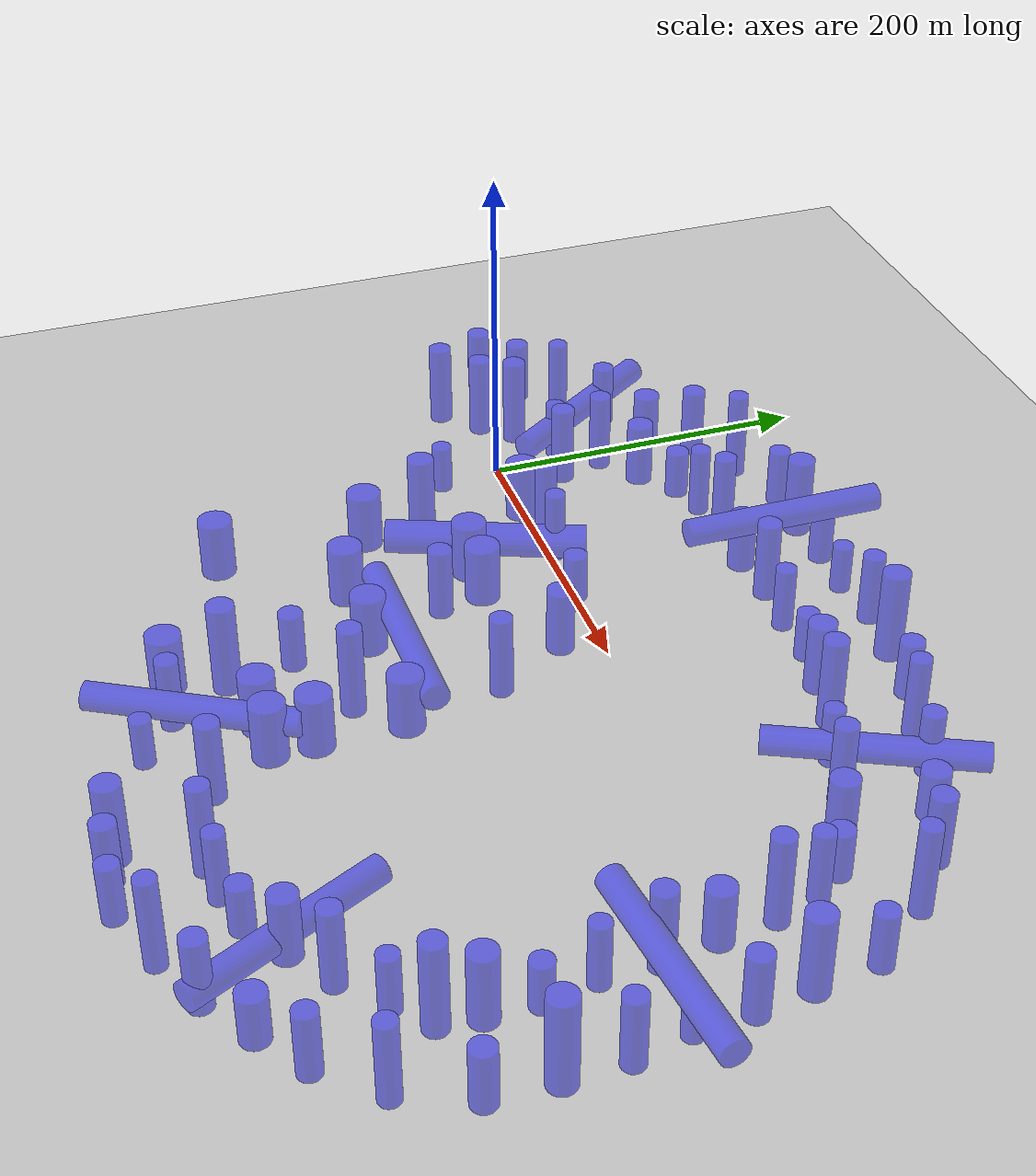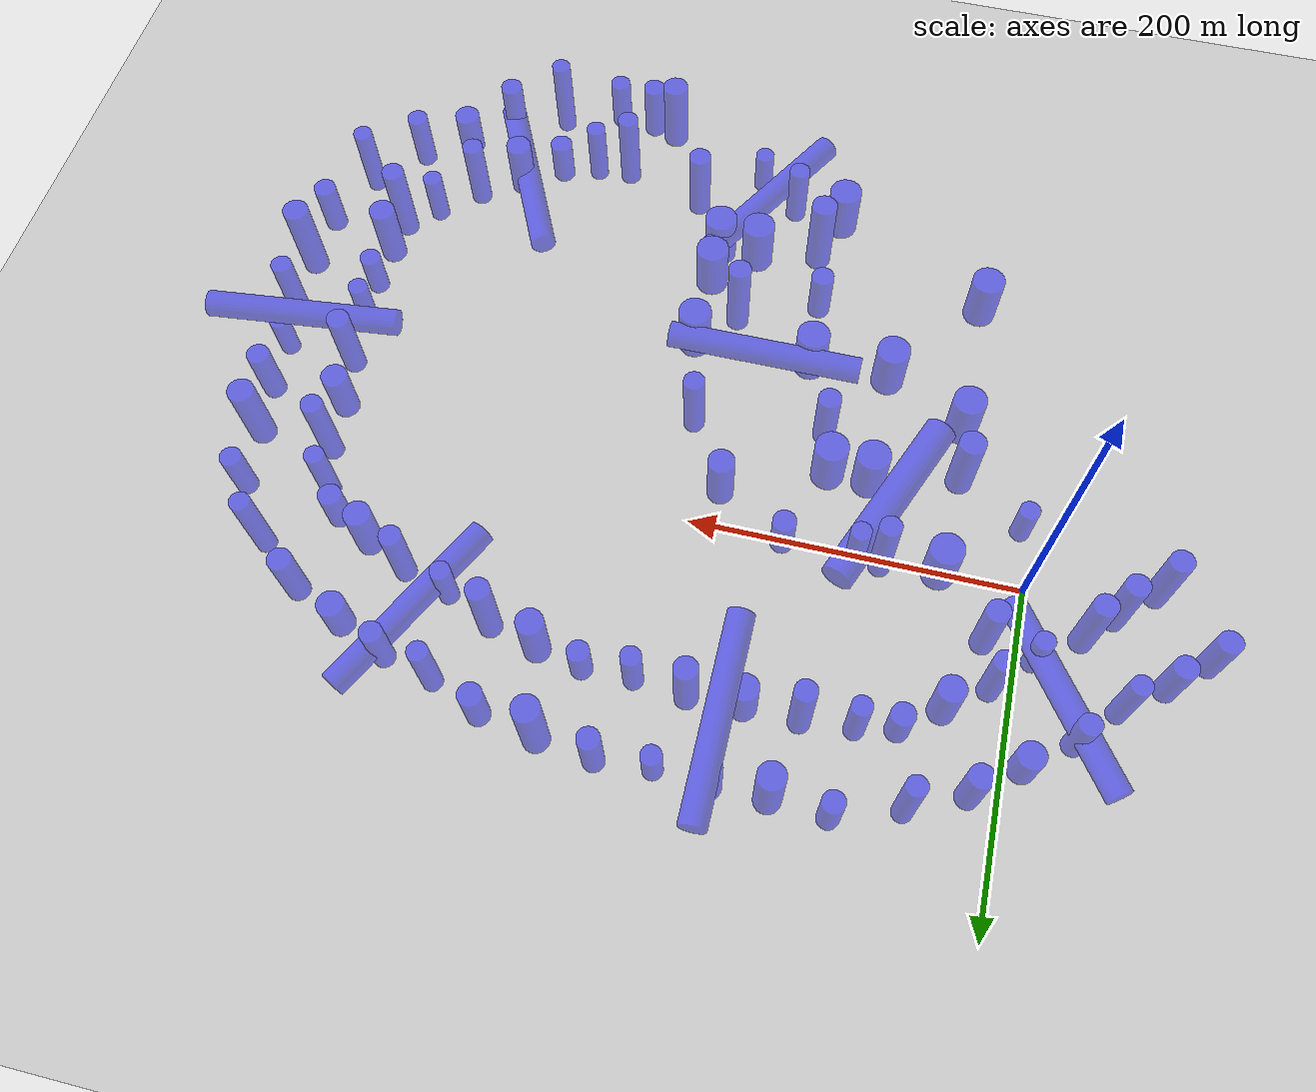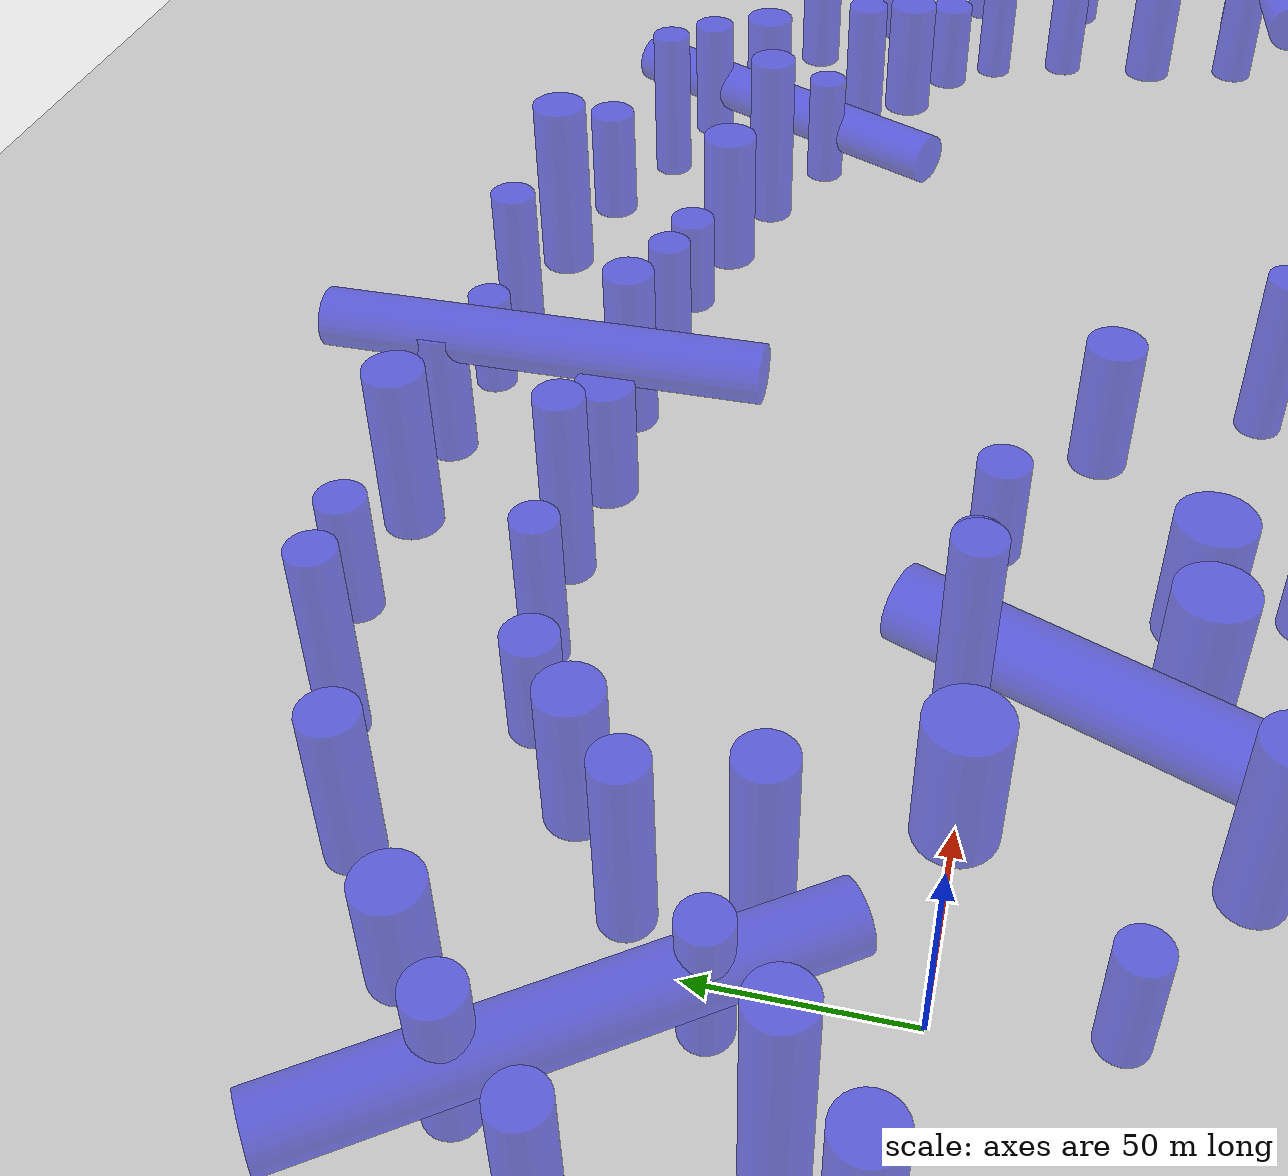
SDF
<?xml version='1.0' encoding='utf-8'?>
<sdf version="1.6">
  <world name="default">
    <physics name="default_physics" default="0" type="ode">
      <ode>
        <solver>
          <type>quick</type>
          <iters>50</iters>
          <sor>0.8</sor>
          <use_dynamic_moi_rescaling>0</use_dynamic_moi_rescaling>
        </solver>
        <constraints>
          <cfm>0</cfm>
          <erp>0.2</erp>
          <contact_max_correcting_vel>0.1</contact_max_correcting_vel>
          <contact_surface_layer>0</contact_surface_layer>
        </constraints>
      </ode>
      <real_time_update_rate>100</real_time_update_rate>
      <max_step_size>0.01</max_step_size>
      <real_time_factor>1</real_time_factor>
    </physics>
    <light name="sun" type="directional">
      <cast_shadows>1</cast_shadows>
      <pose frame="">0 0 10 0 -0 0</pose>
      <diffuse>0.8 0.8 0.8 1</diffuse>
      <specular>0.2 0.2 0.2 1</specular>
      <attenuation>
        <range>1000</range>
        <constant>0.9</constant>
        <linear>0.01</linear>
        <quadratic>0.001</quadratic>
      </attenuation>
      <direction>-0.5 0.1 -0.9</direction>
    </light>
    <model name="ground_plane">
      <static>1</static>
      <link name="link">
        <collision name="collision">
          <geometry>
            <plane>
              <normal>0 0 1</normal>
              <size>1400.0 1400.0</size>
            </plane>
          </geometry>
          <surface>
            <friction>
              <ode>
                <mu>100</mu>
                <mu2>50</mu2>
              </ode>
              <torsional>
                <ode />
              </torsional>
            </friction>
            <contact>
              <ode />
            </contact>
            <bounce />
          </surface>
          <max_contacts>10</max_contacts>
        </collision>
        <visual name="visual">
          <cast_shadows>0</cast_shadows>
          <geometry>
            <plane>
              <normal>0 0 1</normal>
              <size>1400.0 1400.0</size>
            </plane>
          </geometry>
          <material>
            <script>
              <uri>file://media/materials/scripts/gazebo.material</uri>
              <name>Gazebo/Grey</name>
            </script>
          </material>
        </visual>
        <self_collide>0</self_collide>
        <enable_wind>0</enable_wind>
        <kinematic>0</kinematic>
      </link>
    </model>
    <gravity>0 0 0</gravity>
    <magnetic_field>6e-06 2.3e-05 -4.2e-05</magnetic_field>
    <atmosphere type="adiabatic" />
    <scene>
      <ambient>0.4 0.4 0.4 1</ambient>
      <background>0.7 0.7 0.7 1</background>
      <shadows>1</shadows>
    </scene>
    <wind />
    <spherical_coordinates>
      <surface_model>EARTH_WGS84</surface_model>
      <latitude_deg>0</latitude_deg>
      <longitude_deg>0</longitude_deg>
      <elevation>0</elevation>
      <heading_deg>0</heading_deg>
    </spherical_coordinates>
    <model name="suav1">
      <link name="base_link">
        <pose frame="">0 0 0 0 -0 0</pose>
        <inertial>
          <pose frame="">0 0 0 0 -0 0</pose>
          <mass>0.1</mass>
          <inertia>
            <ixx>1</ixx>
            <ixy>0</ixy>
            <ixz>0</ixz>
            <iyy>1</iyy>
            <iyz>0</iyz>
            <izz>1</izz>
          </inertia>
        </inertial>
        <collision name="base_link_fixed_joint_lump__body_link_collision">
          <pose frame="">0 0 0 0 -0 0</pose>
          <geometry>
            <mesh>
              <scale>0.1 0.1 0.1</scale>
              <uri>package://simple_airplane_description/meshes/simple_airplane.dae</uri>
            </mesh>
          </geometry>
          <surface>
            <contact>
              <ode />
            </contact>
            <friction>
              <ode />
              <torsional>
                <ode />
              </torsional>
            </friction>
            <bounce />
          </surface>
          <max_contacts>10</max_contacts>
        </collision>
        <visual name="base_link_fixed_joint_lump__base_visual_visual">
          <pose frame="">0 0 0 0 -0 0</pose>
          <geometry>
            <mesh>
              <scale>0.1 0.1 0.1</scale>
              <uri>package://simple_airplane_description/meshes/simple_airplane.dae</uri>
            </mesh>
          </geometry>
        </visual>
        <velocity_decay />
        <gravity>0</gravity>
        <gravity>1</gravity>
        <velocity_decay />
        <gravity>0</gravity>
        <self_collide>0</self_collide>
        <enable_wind>0</enable_wind>
        <kinematic>0</kinematic>
        <visual name="front_camera_housing">
          <pose>0 0 0.015 0 -0 0</pose>
          <geometry>
            <box>
              <size>0.04 0.05 0.04</size>
            </box>
          </geometry>
        </visual>
        <visual name="front_camera_lens">
          <pose>0.025 0 0.015 0 1.5708 0</pose>
          <geometry>
            <cylinder>
              <length>0.01</length>
              <radius>0.012</radius>
            </cylinder>
          </geometry>
        </visual>
        <sensor name="front_camera" type="camera">
          <pose>0.03 0 0.015 0 0 0</pose>
          <always_on>true</always_on>
          <update_rate>15</update_rate>
          <visualize>false</visualize>
          <camera name="front_camera">
            <horizontal_fov>1.5707963267948966</horizontal_fov>
            <image>
              <width>640</width>
              <height>360</height>
              <format>R8G8B8</format>
            </image>
            <clip>
              <near>0.05</near>
              <far>300</far>
            </clip>
          </camera>
          <plugin filename="libgazebo_ros_camera.so" name="front_camera_controller">
            <robotNamespace>/suav1</robotNamespace>
            <cameraName>front_camera</cameraName>
            <imageTopicName>image_raw</imageTopicName>
            <cameraInfoTopicName>camera_info</cameraInfoTopicName>
            <frameName>front_camera_optical_frame</frameName>
            <updateRate>15.0</updateRate>
          </plugin>
        </sensor>
      </link>
      <static>0</static>
      <plugin name="object_controller" filename="libgazebo_ros_planar_move_with_banking_and_pitching_plugin1.so">
        <commandTopic>cmd_vel</commandTopic>
        <odometryTopic>odom</odometryTopic>
        <odometryFrame>odom</odometryFrame>
        <odometryRate>80.0</odometryRate>
        <robotBaseFrame>base_link</robotBaseFrame>
        <robotNamespace>/suav1/</robotNamespace>
      </plugin>
      <pose frame="">0 0 2 0 -0 0</pose>
    </model>
    <model name="static_obs1">
      <static>true</static>
      <pose frame="">50 0 18.13715 0 0 0</pose>
      <link name="link">
        <inertial>
          <mass>1</mass>
          <inertia>
            <ixx>0.145833</ixx>
            <ixy>0</ixy>
            <ixz>0</ixz>
            <iyy>0.145833</iyy>
            <iyz>0</iyz>
            <izz>0.125</izz>
          </inertia>
          <pose frame="">0 0 0 0 -0 0</pose>
        </inertial>
        <collision name="collision">
          <geometry>
            <cylinder>
              <radius>10.1458</radius>
              <length>36.2743</length>
            </cylinder>
          </geometry>
          <max_contacts>10</max_contacts>
          <surface>
            <contact>
              <ode />
            </contact>
            <bounce />
            <friction>
              <torsional>
                <ode />
              </torsional>
              <ode />
            </friction>
          </surface>
        </collision>
        <visual name="visual">
          <geometry>
            <cylinder>
              <radius>10.1458</radius>
              <length>36.2743</length>
            </cylinder>
          </geometry>
          <material>
            <ambient>0 0 1 1</ambient>
            <diffuse>0 0 1 1</diffuse>
          </material>
          <transparency>0.5</transparency>
        </visual>
        <self_collide>0</self_collide>
        <enable_wind>0</enable_wind>
        <kinematic>0</kinematic>
      </link>
    </model>
    <model name="unit_cylinder_clone">
      <static>true</static>
      <pose frame="">100.023 -50.0251 18.13715 0 0 0</pose>
      <link name="link">
        <inertial>
          <mass>1</mass>
          <inertia>
            <ixx>0.145833</ixx>
            <ixy>0</ixy>
            <ixz>0</ixz>
            <iyy>0.145833</iyy>
            <iyz>0</iyz>
            <izz>0.125</izz>
          </inertia>
          <pose frame="">0 0 0 0 -0 0</pose>
        </inertial>
        <collision name="collision">
          <geometry>
            <cylinder>
              <radius>10.1458</radius>
              <length>36.2743</length>
            </cylinder>
          </geometry>
          <max_contacts>10</max_contacts>
          <surface>
            <contact>
              <ode />
            </contact>
            <bounce />
            <friction>
              <torsional>
                <ode />
              </torsional>
              <ode />
            </friction>
          </surface>
        </collision>
        <visual name="visual">
          <geometry>
            <cylinder>
              <radius>10.1458</radius>
              <length>36.2743</length>
            </cylinder>
          </geometry>
          <material>
            <ambient>0 0 1 1</ambient>
            <diffuse>0 0 1 1</diffuse>
          </material>
          <transparency>0.5</transparency>
        </visual>
        <self_collide>0</self_collide>
        <enable_wind>0</enable_wind>
        <kinematic>0</kinematic>
      </link>
    </model>
    <model name="unit_cylinder_clone_0">
      <static>true</static>
      <pose frame="">125.023 -50.0251 18.13715 0 0 0</pose>
      <link name="link">
        <inertial>
          <mass>1</mass>
          <inertia>
            <ixx>0.145833</ixx>
            <ixy>0</ixy>
            <ixz>0</ixz>
            <iyy>0.145833</iyy>
            <iyz>0</iyz>
            <izz>0.125</izz>
          </inertia>
          <pose frame="">0 0 0 0 -0 0</pose>
        </inertial>
        <collision name="collision">
          <geometry>
            <cylinder>
              <radius>10.1458</radius>
              <length>36.2743</length>
            </cylinder>
          </geometry>
          <max_contacts>10</max_contacts>
          <surface>
            <contact>
              <ode />
            </contact>
            <bounce />
            <friction>
              <torsional>
                <ode />
              </torsional>
              <ode />
            </friction>
          </surface>
        </collision>
        <visual name="visual">
          <geometry>
            <cylinder>
              <radius>10.1458</radius>
              <length>36.2743</length>
            </cylinder>
          </geometry>
          <material>
            <ambient>0 0 1 1</ambient>
            <diffuse>0 0 1 1</diffuse>
          </material>
          <transparency>0.5</transparency>
        </visual>
        <self_collide>0</self_collide>
        <enable_wind>0</enable_wind>
        <kinematic>0</kinematic>
      </link>
    </model>
    <model name="unit_cylinder_clone_1">
      <static>true</static>
      <pose frame="">50.0229 -100.025 18.13715 0 0 0</pose>
      <link name="link">
        <inertial>
          <mass>1</mass>
          <inertia>
            <ixx>0.145833</ixx>
            <ixy>0</ixy>
            <ixz>0</ixz>
            <iyy>0.145833</iyy>
            <iyz>0</iyz>
            <izz>0.125</izz>
          </inertia>
          <pose frame="">0 0 0 0 -0 0</pose>
        </inertial>
        <collision name="collision">
          <geometry>
            <cylinder>
              <radius>10.1458</radius>
              <length>36.2743</length>
            </cylinder>
          </geometry>
          <max_contacts>10</max_contacts>
          <surface>
            <contact>
              <ode />
            </contact>
            <bounce />
            <friction>
              <torsional>
                <ode />
              </torsional>
              <ode />
            </friction>
          </surface>
        </collision>
        <visual name="visual">
          <geometry>
            <cylinder>
              <radius>10.1458</radius>
              <length>36.2743</length>
            </cylinder>
          </geometry>
          <material>
            <ambient>0 0 1 1</ambient>
            <diffuse>0 0 1 1</diffuse>
          </material>
          <transparency>0.5</transparency>
        </visual>
        <self_collide>0</self_collide>
        <enable_wind>0</enable_wind>
        <kinematic>0</kinematic>
      </link>
    </model>
    <model name="unit_cylinder_clone_2">
      <static>true</static>
      <pose frame="">100.133 -125.017 18.13715 0 0 0</pose>
      <link name="link">
        <inertial>
          <mass>1</mass>
          <inertia>
            <ixx>0.145833</ixx>
            <ixy>0</ixy>
            <ixz>0</ixz>
            <iyy>0.145833</iyy>
            <iyz>0</iyz>
            <izz>0.125</izz>
          </inertia>
          <pose frame="">0 0 0 0 -0 0</pose>
        </inertial>
        <collision name="collision">
          <geometry>
            <cylinder>
              <radius>10.1458</radius>
              <length>36.2743</length>
            </cylinder>
          </geometry>
          <max_contacts>10</max_contacts>
          <surface>
            <contact>
              <ode />
            </contact>
            <bounce />
            <friction>
              <torsional>
                <ode />
              </torsional>
              <ode />
            </friction>
          </surface>
        </collision>
        <visual name="visual">
          <geometry>
            <cylinder>
              <radius>10.1458</radius>
              <length>36.2743</length>
            </cylinder>
          </geometry>
          <material>
            <ambient>0 0 1 1</ambient>
            <diffuse>0 0 1 1</diffuse>
          </material>
          <transparency>0.5</transparency>
        </visual>
        <self_collide>0</self_collide>
        <enable_wind>0</enable_wind>
        <kinematic>0</kinematic>
      </link>
    </model>
    <model name="unit_cylinder_clone_3_clone">
      <static>true</static>
      <pose frame="">225.023 -125.025 18.13715 0 0 0</pose>
      <link name="link">
        <inertial>
          <mass>1</mass>
          <inertia>
            <ixx>0.145833</ixx>
            <ixy>0</ixy>
            <ixz>0</ixz>
            <iyy>0.145833</iyy>
            <iyz>0</iyz>
            <izz>0.125</izz>
          </inertia>
          <pose frame="">0 0 0 0 -0 0</pose>
        </inertial>
        <collision name="collision">
          <geometry>
            <cylinder>
              <radius>10.1458</radius>
              <length>36.2743</length>
            </cylinder>
          </geometry>
          <max_contacts>10</max_contacts>
          <surface>
            <contact>
              <ode />
            </contact>
            <bounce />
            <friction>
              <torsional>
                <ode />
              </torsional>
              <ode />
            </friction>
          </surface>
        </collision>
        <visual name="visual">
          <geometry>
            <cylinder>
              <radius>10.1458</radius>
              <length>36.2743</length>
            </cylinder>
          </geometry>
          <material>
            <ambient>0 0 1 1</ambient>
            <diffuse>0 0 1 1</diffuse>
          </material>
          <transparency>0.5</transparency>
        </visual>
        <self_collide>0</self_collide>
        <enable_wind>0</enable_wind>
        <kinematic>0</kinematic>
      </link>
    </model>
    <model name="unit_cylinder_clone_3_clone_0">
      <static>true</static>
      <pose frame="">50.0229 -190.025 18.13715 0 0 0</pose>
      <link name="link">
        <inertial>
          <mass>1</mass>
          <inertia>
            <ixx>0.145833</ixx>
            <ixy>0</ixy>
            <ixz>0</ixz>
            <iyy>0.145833</iyy>
            <iyz>0</iyz>
            <izz>0.125</izz>
          </inertia>
          <pose frame="">0 0 0 0 -0 0</pose>
        </inertial>
        <collision name="collision">
          <geometry>
            <cylinder>
              <radius>10.1458</radius>
              <length>36.2743</length>
            </cylinder>
          </geometry>
          <max_contacts>10</max_contacts>
          <surface>
            <contact>
              <ode />
            </contact>
            <bounce />
            <friction>
              <torsional>
                <ode />
              </torsional>
              <ode />
            </friction>
          </surface>
        </collision>
        <visual name="visual">
          <geometry>
            <cylinder>
              <radius>10.1458</radius>
              <length>36.2743</length>
            </cylinder>
          </geometry>
          <material>
            <ambient>0 0 1 1</ambient>
            <diffuse>0 0 1 1</diffuse>
          </material>
          <transparency>0.5</transparency>
        </visual>
        <self_collide>0</self_collide>
        <enable_wind>0</enable_wind>
        <kinematic>0</kinematic>
      </link>
    </model>
    <model name="unit_cylinder_clone_3_clone_0_clone">
      <static>true</static>
      <pose frame="">150.023 -125.025 18.13715 0 0 0</pose>
      <link name="link">
        <inertial>
          <mass>1</mass>
          <inertia>
            <ixx>0.145833</ixx>
            <ixy>0</ixy>
            <ixz>0</ixz>
            <iyy>0.145833</iyy>
            <iyz>0</iyz>
            <izz>0.125</izz>
          </inertia>
          <pose frame="">0 0 0 0 -0 0</pose>
        </inertial>
        <collision name="collision">
          <geometry>
            <cylinder>
              <radius>10.1458</radius>
              <length>36.2743</length>
            </cylinder>
          </geometry>
          <max_contacts>10</max_contacts>
          <surface>
            <contact>
              <ode />
            </contact>
            <bounce />
            <friction>
              <torsional>
                <ode />
              </torsional>
              <ode />
            </friction>
          </surface>
        </collision>
        <visual name="visual">
          <geometry>
            <cylinder>
              <radius>10.1458</radius>
              <length>36.2743</length>
            </cylinder>
          </geometry>
          <material>
            <ambient>0 0 1 1</ambient>
            <diffuse>0 0 1 1</diffuse>
          </material>
          <transparency>0.5</transparency>
        </visual>
        <self_collide>0</self_collide>
        <enable_wind>0</enable_wind>
        <kinematic>0</kinematic>
      </link>
    </model>
    <model name="unit_cylinder_clone_3_clone_0_clone_0">
      <static>true</static>
      <pose frame="">225.023 -200.025 18.13715 0 0 0</pose>
      <link name="link">
        <inertial>
          <mass>1</mass>
          <inertia>
            <ixx>0.145833</ixx>
            <ixy>0</ixy>
            <ixz>0</ixz>
            <iyy>0.145833</iyy>
            <iyz>0</iyz>
            <izz>0.125</izz>
          </inertia>
          <pose frame="">0 0 0 0 -0 0</pose>
        </inertial>
        <collision name="collision">
          <geometry>
            <cylinder>
              <radius>10.1458</radius>
              <length>36.2743</length>
            </cylinder>
          </geometry>
          <max_contacts>10</max_contacts>
          <surface>
            <contact>
              <ode />
            </contact>
            <bounce />
            <friction>
              <torsional>
                <ode />
              </torsional>
              <ode />
            </friction>
          </surface>
        </collision>
        <visual name="visual">
          <geometry>
            <cylinder>
              <radius>10.1458</radius>
              <length>36.2743</length>
            </cylinder>
          </geometry>
          <material>
            <ambient>0 0 1 1</ambient>
            <diffuse>0 0 1 1</diffuse>
          </material>
          <transparency>0.5</transparency>
        </visual>
        <self_collide>0</self_collide>
        <enable_wind>0</enable_wind>
        <kinematic>0</kinematic>
      </link>
    </model>
    <model name="unit_cylinder_clone_3_clone_0_clone_0_clone">
      <static>true</static>
      <pose frame="">225.023 -175.025 18.13715 0 0 0</pose>
      <link name="link">
        <inertial>
          <mass>1</mass>
          <inertia>
            <ixx>0.145833</ixx>
            <ixy>0</ixy>
            <ixz>0</ixz>
            <iyy>0.145833</iyy>
            <iyz>0</iyz>
            <izz>0.125</izz>
          </inertia>
          <pose frame="">0 0 0 0 -0 0</pose>
        </inertial>
        <collision name="collision">
          <geometry>
            <cylinder>
              <radius>10.1458</radius>
              <length>36.2743</length>
            </cylinder>
          </geometry>
          <max_contacts>10</max_contacts>
          <surface>
            <contact>
              <ode />
            </contact>
            <bounce />
            <friction>
              <torsional>
                <ode />
              </torsional>
              <ode />
            </friction>
          </surface>
        </collision>
        <visual name="visual">
          <geometry>
            <cylinder>
              <radius>10.1458</radius>
              <length>36.2743</length>
            </cylinder>
          </geometry>
          <material>
            <ambient>0 0 1 1</ambient>
            <diffuse>0 0 1 1</diffuse>
          </material>
          <transparency>0.5</transparency>
        </visual>
        <self_collide>0</self_collide>
        <enable_wind>0</enable_wind>
        <kinematic>0</kinematic>
      </link>
    </model>
    <model name="unit_cylinder_clone_3_clone_0_clone_0_clone_clone">
      <static>true</static>
      <pose frame="">200.023 -200.025 18.13715 0 0 0</pose>
      <link name="link">
        <inertial>
          <mass>1</mass>
          <inertia>
            <ixx>0.145833</ixx>
            <ixy>0</ixy>
            <ixz>0</ixz>
            <iyy>0.145833</iyy>
            <iyz>0</iyz>
            <izz>0.125</izz>
          </inertia>
          <pose frame="">0 0 0 0 -0 0</pose>
        </inertial>
        <collision name="collision">
          <geometry>
            <cylinder>
              <radius>10.1458</radius>
              <length>36.2743</length>
            </cylinder>
          </geometry>
          <max_contacts>10</max_contacts>
          <surface>
            <contact>
              <ode />
            </contact>
            <bounce />
            <friction>
              <torsional>
                <ode />
              </torsional>
              <ode />
            </friction>
          </surface>
        </collision>
        <visual name="visual">
          <geometry>
            <cylinder>
              <radius>10.1458</radius>
              <length>36.2743</length>
            </cylinder>
          </geometry>
          <material>
            <ambient>0 0 1 1</ambient>
            <diffuse>0 0 1 1</diffuse>
          </material>
          <transparency>0.5</transparency>
        </visual>
        <self_collide>0</self_collide>
        <enable_wind>0</enable_wind>
        <kinematic>0</kinematic>
      </link>
    </model>
    <model name="unit_cylinder_clone_3_clone_0_clone_1">
      <static>true</static>
      <pose frame="">150.023 -240.025 18.13715 0 0 0</pose>
      <link name="link">
        <inertial>
          <mass>1</mass>
          <inertia>
            <ixx>0.145833</ixx>
            <ixy>0</ixy>
            <ixz>0</ixz>
            <iyy>0.145833</iyy>
            <iyz>0</iyz>
            <izz>0.125</izz>
          </inertia>
          <pose frame="">0 0 0 0 -0 0</pose>
        </inertial>
        <collision name="collision">
          <geometry>
            <cylinder>
              <radius>10.1458</radius>
              <length>36.2743</length>
            </cylinder>
          </geometry>
          <max_contacts>10</max_contacts>
          <surface>
            <contact>
              <ode />
            </contact>
            <bounce />
            <friction>
              <torsional>
                <ode />
              </torsional>
              <ode />
            </friction>
          </surface>
        </collision>
        <visual name="visual">
          <geometry>
            <cylinder>
              <radius>10.1458</radius>
              <length>36.2743</length>
            </cylinder>
          </geometry>
          <material>
            <ambient>0 0 1 1</ambient>
            <diffuse>0 0 1 1</diffuse>
          </material>
          <transparency>0.5</transparency>
        </visual>
        <self_collide>0</self_collide>
        <enable_wind>0</enable_wind>
        <kinematic>0</kinematic>
      </link>
    </model>
    <gui fullscreen="0">
      <camera name="user_camera">
        <pose frame="">210.0 -530.0 430.0 0.0 0.85 1.5707963268</pose>
        <view_controller>orbit</view_controller>
        <projection_type>perspective</projection_type>
      </camera>
    </gui>
    <model name="static_obs13">
      <static>true</static>
      <pose>6.27 -38.06 15.0 0 0 0</pose>
      <link name="link">
        <gravity>false</gravity>
        <collision name="collision">
          <geometry>
            <cylinder>
              <radius>6.0</radius>
              <length>30.0</length>
            </cylinder>
          </geometry>
        </collision>
        <visual name="visual">
          <geometry>
            <cylinder>
              <radius>6.0</radius>
              <length>30.0</length>
            </cylinder>
          </geometry>
          <material>
            <ambient>0 0 1 1</ambient>
            <diffuse>0 0 1 1</diffuse>
          </material>
          <transparency>0.5</transparency>
        </visual>
      </link>
    </model>
    <model name="static_obs14">
      <static>true</static>
      <pose>19.63 36.94 25.0 0 0 0</pose>
      <link name="link">
        <gravity>false</gravity>
        <collision name="collision">
          <geometry>
            <cylinder>
              <radius>7.0</radius>
              <length>50.0</length>
            </cylinder>
          </geometry>
        </collision>
        <visual name="visual">
          <geometry>
            <cylinder>
              <radius>7.0</radius>
              <length>50.0</length>
            </cylinder>
          </geometry>
          <material>
            <ambient>0 0 1 1</ambient>
            <diffuse>0 0 1 1</diffuse>
          </material>
          <transparency>0.5</transparency>
        </visual>
      </link>
    </model>
    <model name="static_obs15">
      <static>true</static>
      <pose>46.3 -63.21 25.0 0 0 0</pose>
      <link name="link">
        <gravity>false</gravity>
        <collision name="collision">
          <geometry>
            <cylinder>
              <radius>8.0</radius>
              <length>50.0</length>
            </cylinder>
          </geometry>
        </collision>
        <visual name="visual">
          <geometry>
            <cylinder>
              <radius>8.0</radius>
              <length>50.0</length>
            </cylinder>
          </geometry>
          <material>
            <ambient>0 0 1 1</ambient>
            <diffuse>0 0 1 1</diffuse>
          </material>
          <transparency>0.5</transparency>
        </visual>
      </link>
    </model>
    <model name="static_obs16">
      <static>true</static>
      <pose>84.32 3.23 28.0 0 0 0</pose>
      <link name="link">
        <gravity>false</gravity>
        <collision name="collision">
          <geometry>
            <cylinder>
              <radius>6.5</radius>
              <length>56.0</length>
            </cylinder>
          </geometry>
        </collision>
        <visual name="visual">
          <geometry>
            <cylinder>
              <radius>6.5</radius>
              <length>56.0</length>
            </cylinder>
          </geometry>
          <material>
            <ambient>0 0 1 1</ambient>
            <diffuse>0 0 1 1</diffuse>
          </material>
          <transparency>0.5</transparency>
        </visual>
      </link>
    </model>
    <model name="static_obs17">
      <static>true</static>
      <pose>99.32 3.91 22.0 0 0 0</pose>
      <link name="link">
        <gravity>false</gravity>
        <collision name="collision">
          <geometry>
            <cylinder>
              <radius>6.0</radius>
              <length>44.0</length>
            </cylinder>
          </geometry>
        </collision>
        <visual name="visual">
          <geometry>
            <cylinder>
              <radius>6.0</radius>
              <length>44.0</length>
            </cylinder>
          </geometry>
          <material>
            <ambient>0 0 1 1</ambient>
            <diffuse>0 0 1 1</diffuse>
          </material>
          <transparency>0.5</transparency>
        </visual>
      </link>
    </model>
    <model name="static_obs18">
      <static>true</static>
      <pose>143.06 0.77 15.0 0 0 0</pose>
      <link name="link">
        <gravity>false</gravity>
        <collision name="collision">
          <geometry>
            <cylinder>
              <radius>7.0</radius>
              <length>30.0</length>
            </cylinder>
          </geometry>
        </collision>
        <visual name="visual">
          <geometry>
            <cylinder>
              <radius>7.0</radius>
              <length>30.0</length>
            </cylinder>
          </geometry>
          <material>
            <ambient>0 0 1 1</ambient>
            <diffuse>0 0 1 1</diffuse>
          </material>
          <transparency>0.5</transparency>
        </visual>
      </link>
    </model>
    <model name="static_obs19">
      <static>true</static>
      <pose>132.02 -77.37 22.0 0 0 0</pose>
      <link name="link">
        <gravity>false</gravity>
        <collision name="collision">
          <geometry>
            <cylinder>
              <radius>7.0</radius>
              <length>44.0</length>
            </cylinder>
          </geometry>
        </collision>
        <visual name="visual">
          <geometry>
            <cylinder>
              <radius>7.0</radius>
              <length>44.0</length>
            </cylinder>
          </geometry>
          <material>
            <ambient>0 0 1 1</ambient>
            <diffuse>0 0 1 1</diffuse>
          </material>
          <transparency>0.5</transparency>
        </visual>
      </link>
    </model>
    <model name="static_obs20">
      <static>true</static>
      <pose>185.89 -23.61 20.0 0 0 0</pose>
      <link name="link">
        <gravity>false</gravity>
        <collision name="collision">
          <geometry>
            <cylinder>
              <radius>8.0</radius>
              <length>40.0</length>
            </cylinder>
          </geometry>
        </collision>
        <visual name="visual">
          <geometry>
            <cylinder>
              <radius>8.0</radius>
              <length>40.0</length>
            </cylinder>
          </geometry>
          <material>
            <ambient>0 0 1 1</ambient>
            <diffuse>0 0 1 1</diffuse>
          </material>
          <transparency>0.5</transparency>
        </visual>
      </link>
    </model>
    <model name="static_obs21">
      <static>true</static>
      <pose>212.28 -67.25 25.0 0 0 0</pose>
      <link name="link">
        <gravity>false</gravity>
        <collision name="collision">
          <geometry>
            <cylinder>
              <radius>6.5</radius>
              <length>50.0</length>
            </cylinder>
          </geometry>
        </collision>
        <visual name="visual">
          <geometry>
            <cylinder>
              <radius>6.5</radius>
              <length>50.0</length>
            </cylinder>
          </geometry>
          <material>
            <ambient>0 0 1 1</ambient>
            <diffuse>0 0 1 1</diffuse>
          </material>
          <transparency>0.5</transparency>
        </visual>
      </link>
    </model>
    <model name="static_obs22">
      <static>true</static>
      <pose>202.16 -148.57 28.0 0 0 0</pose>
      <link name="link">
        <gravity>false</gravity>
        <collision name="collision">
          <geometry>
            <cylinder>
              <radius>7.0</radius>
              <length>56.0</length>
            </cylinder>
          </geometry>
        </collision>
        <visual name="visual">
          <geometry>
            <cylinder>
              <radius>7.0</radius>
              <length>56.0</length>
            </cylinder>
          </geometry>
          <material>
            <ambient>0 0 1 1</ambient>
            <diffuse>0 0 1 1</diffuse>
          </material>
          <transparency>0.5</transparency>
        </visual>
      </link>
    </model>
    <model name="static_obs23">
      <static>true</static>
      <pose>152.5 -169.68 18.0 0 0 0</pose>
      <link name="link">
        <gravity>false</gravity>
        <collision name="collision">
          <geometry>
            <cylinder>
              <radius>7.0</radius>
              <length>36.0</length>
            </cylinder>
          </geometry>
        </collision>
        <visual name="visual">
          <geometry>
            <cylinder>
              <radius>7.0</radius>
              <length>36.0</length>
            </cylinder>
          </geometry>
          <material>
            <ambient>0 0 1 1</ambient>
            <diffuse>0 0 1 1</diffuse>
          </material>
          <transparency>0.5</transparency>
        </visual>
      </link>
    </model>
    <model name="static_obs24">
      <static>true</static>
      <pose>160.38 -209.07 28.0 0 0 0</pose>
      <link name="link">
        <gravity>false</gravity>
        <collision name="collision">
          <geometry>
            <cylinder>
              <radius>8.0</radius>
              <length>56.0</length>
            </cylinder>
          </geometry>
        </collision>
        <visual name="visual">
          <geometry>
            <cylinder>
              <radius>8.0</radius>
              <length>56.0</length>
            </cylinder>
          </geometry>
          <material>
            <ambient>0 0 1 1</ambient>
            <diffuse>0 0 1 1</diffuse>
          </material>
          <transparency>0.5</transparency>
        </visual>
      </link>
    </model>
    <model name="static_obs25">
      <static>true</static>
      <pose>182.15 -243.8 22.0 0 0 0</pose>
      <link name="link">
        <gravity>false</gravity>
        <collision name="collision">
          <geometry>
            <cylinder>
              <radius>6.5</radius>
              <length>44.0</length>
            </cylinder>
          </geometry>
        </collision>
        <visual name="visual">
          <geometry>
            <cylinder>
              <radius>6.5</radius>
              <length>44.0</length>
            </cylinder>
          </geometry>
          <material>
            <ambient>0 0 1 1</ambient>
            <diffuse>0 0 1 1</diffuse>
          </material>
          <transparency>0.5</transparency>
        </visual>
      </link>
    </model>
    <model name="static_obs26">
      <static>true</static>
      <pose>208.76 -263.97 15.0 0 0 0</pose>
      <link name="link">
        <gravity>false</gravity>
        <collision name="collision">
          <geometry>
            <cylinder>
              <radius>6.0</radius>
              <length>30.0</length>
            </cylinder>
          </geometry>
        </collision>
        <visual name="visual">
          <geometry>
            <cylinder>
              <radius>6.0</radius>
              <length>30.0</length>
            </cylinder>
          </geometry>
          <material>
            <ambient>0 0 1 1</ambient>
            <diffuse>0 0 1 1</diffuse>
          </material>
          <transparency>0.5</transparency>
        </visual>
      </link>
    </model>
    <model name="static_obs27">
      <static>true</static>
      <pose>247.28 -235.31 25.0 0 0 0</pose>
      <link name="link">
        <gravity>false</gravity>
        <collision name="collision">
          <geometry>
            <cylinder>
              <radius>7.0</radius>
              <length>50.0</length>
            </cylinder>
          </geometry>
        </collision>
        <visual name="visual">
          <geometry>
            <cylinder>
              <radius>7.0</radius>
              <length>50.0</length>
            </cylinder>
          </geometry>
          <material>
            <ambient>0 0 1 1</ambient>
            <diffuse>0 0 1 1</diffuse>
          </material>
          <transparency>0.5</transparency>
        </visual>
      </link>
    </model>
    <model name="static_obs28">
      <static>true</static>
      <pose>293.27 -296.57 20.0 0 0 0</pose>
      <link name="link">
        <gravity>false</gravity>
        <collision name="collision">
          <geometry>
            <cylinder>
              <radius>7.0</radius>
              <length>40.0</length>
            </cylinder>
          </geometry>
        </collision>
        <visual name="visual">
          <geometry>
            <cylinder>
              <radius>7.0</radius>
              <length>40.0</length>
            </cylinder>
          </geometry>
          <material>
            <ambient>0 0 1 1</ambient>
            <diffuse>0 0 1 1</diffuse>
          </material>
          <transparency>0.5</transparency>
        </visual>
      </link>
    </model>
    <model name="static_obs29">
      <static>true</static>
      <pose>276.98 -291.29 25.0 0 0 0</pose>
      <link name="link">
        <gravity>false</gravity>
        <collision name="collision">
          <geometry>
            <cylinder>
              <radius>8.0</radius>
              <length>50.0</length>
            </cylinder>
          </geometry>
        </collision>
        <visual name="visual">
          <geometry>
            <cylinder>
              <radius>8.0</radius>
              <length>50.0</length>
            </cylinder>
          </geometry>
          <material>
            <ambient>0 0 1 1</ambient>
            <diffuse>0 0 1 1</diffuse>
          </material>
          <transparency>0.5</transparency>
        </visual>
      </link>
    </model>
    <model name="static_obs30">
      <static>true</static>
      <pose>299.46 -250.24 28.0 0 0 0</pose>
      <link name="link">
        <gravity>false</gravity>
        <collision name="collision">
          <geometry>
            <cylinder>
              <radius>6.5</radius>
              <length>56.0</length>
            </cylinder>
          </geometry>
        </collision>
        <visual name="visual">
          <geometry>
            <cylinder>
              <radius>6.5</radius>
              <length>56.0</length>
            </cylinder>
          </geometry>
          <material>
            <ambient>0 0 1 1</ambient>
            <diffuse>0 0 1 1</diffuse>
          </material>
          <transparency>0.5</transparency>
        </visual>
      </link>
    </model>
    <model name="static_obs31">
      <static>true</static>
      <pose>318.0 -299.13 18.0 0 0 0</pose>
      <link name="link">
        <gravity>false</gravity>
        <collision name="collision">
          <geometry>
            <cylinder>
              <radius>6.5</radius>
              <length>36.0</length>
            </cylinder>
          </geometry>
        </collision>
        <visual name="visual">
          <geometry>
            <cylinder>
              <radius>6.5</radius>
              <length>36.0</length>
            </cylinder>
          </geometry>
          <material>
            <ambient>0 0 1 1</ambient>
            <diffuse>0 0 1 1</diffuse>
          </material>
          <transparency>0.5</transparency>
        </visual>
      </link>
    </model>
    <model name="static_obs32">
      <static>true</static>
      <pose>321.46 -248.19 22.0 0 0 0</pose>
      <link name="link">
        <gravity>false</gravity>
        <collision name="collision">
          <geometry>
            <cylinder>
              <radius>6.0</radius>
              <length>44.0</length>
            </cylinder>
          </geometry>
        </collision>
        <visual name="visual">
          <geometry>
            <cylinder>
              <radius>6.0</radius>
              <length>44.0</length>
            </cylinder>
          </geometry>
          <material>
            <ambient>0 0 1 1</ambient>
            <diffuse>0 0 1 1</diffuse>
          </material>
          <transparency>0.5</transparency>
        </visual>
      </link>
    </model>
    <model name="static_obs33">
      <static>true</static>
      <pose>355.22 -285.95 28.0 0 0 0</pose>
      <link name="link">
        <gravity>false</gravity>
        <collision name="collision">
          <geometry>
            <cylinder>
              <radius>6.0</radius>
              <length>56.0</length>
            </cylinder>
          </geometry>
        </collision>
        <visual name="visual">
          <geometry>
            <cylinder>
              <radius>6.0</radius>
              <length>56.0</length>
            </cylinder>
          </geometry>
          <material>
            <ambient>0 0 1 1</ambient>
            <diffuse>0 0 1 1</diffuse>
          </material>
          <transparency>0.5</transparency>
        </visual>
      </link>
    </model>
    <model name="static_obs34">
      <static>true</static>
      <pose>345.01 -242.19 15.0 0 0 0</pose>
      <link name="link">
        <gravity>false</gravity>
        <collision name="collision">
          <geometry>
            <cylinder>
              <radius>7.0</radius>
              <length>30.0</length>
            </cylinder>
          </geometry>
        </collision>
        <visual name="visual">
          <geometry>
            <cylinder>
              <radius>7.0</radius>
              <length>30.0</length>
            </cylinder>
          </geometry>
          <material>
            <ambient>0 0 1 1</ambient>
            <diffuse>0 0 1 1</diffuse>
          </material>
          <transparency>0.5</transparency>
        </visual>
      </link>
    </model>
    <model name="static_obs35">
      <static>true</static>
      <pose>387.07 -271.34 22.0 0 0 0</pose>
      <link name="link">
        <gravity>false</gravity>
        <collision name="collision">
          <geometry>
            <cylinder>
              <radius>7.0</radius>
              <length>44.0</length>
            </cylinder>
          </geometry>
        </collision>
        <visual name="visual">
          <geometry>
            <cylinder>
              <radius>7.0</radius>
              <length>44.0</length>
            </cylinder>
          </geometry>
          <material>
            <ambient>0 0 1 1</ambient>
            <diffuse>0 0 1 1</diffuse>
          </material>
          <transparency>0.5</transparency>
        </visual>
      </link>
    </model>
    <model name="static_obs36">
      <static>true</static>
      <pose>369.22 -225.98 20.0 0 0 0</pose>
      <link name="link">
        <gravity>false</gravity>
        <collision name="collision">
          <geometry>
            <cylinder>
              <radius>8.0</radius>
              <length>40.0</length>
            </cylinder>
          </geometry>
        </collision>
        <visual name="visual">
          <geometry>
            <cylinder>
              <radius>8.0</radius>
              <length>40.0</length>
            </cylinder>
          </geometry>
          <material>
            <ambient>0 0 1 1</ambient>
            <diffuse>0 0 1 1</diffuse>
          </material>
          <transparency>0.5</transparency>
        </visual>
      </link>
    </model>
    <model name="static_obs37">
      <static>true</static>
      <pose>414.82 -252.03 15.0 0 0 0</pose>
      <link name="link">
        <gravity>false</gravity>
        <collision name="collision">
          <geometry>
            <cylinder>
              <radius>8.0</radius>
              <length>30.0</length>
            </cylinder>
          </geometry>
        </collision>
        <visual name="visual">
          <geometry>
            <cylinder>
              <radius>8.0</radius>
              <length>30.0</length>
            </cylinder>
          </geometry>
          <material>
            <ambient>0 0 1 1</ambient>
            <diffuse>0 0 1 1</diffuse>
          </material>
          <transparency>0.5</transparency>
        </visual>
      </link>
    </model>
    <model name="static_obs38">
      <static>true</static>
      <pose>394.7 -209.81 25.0 0 0 0</pose>
      <link name="link">
        <gravity>false</gravity>
        <collision name="collision">
          <geometry>
            <cylinder>
              <radius>6.5</radius>
              <length>50.0</length>
            </cylinder>
          </geometry>
        </collision>
        <visual name="visual">
          <geometry>
            <cylinder>
              <radius>6.5</radius>
              <length>50.0</length>
            </cylinder>
          </geometry>
          <material>
            <ambient>0 0 1 1</ambient>
            <diffuse>0 0 1 1</diffuse>
          </material>
          <transparency>0.5</transparency>
        </visual>
      </link>
    </model>
    <model name="static_obs39">
      <static>true</static>
      <pose>442.42 -233.61 20.0 0 0 0</pose>
      <link name="link">
        <gravity>false</gravity>
        <collision name="collision">
          <geometry>
            <cylinder>
              <radius>6.5</radius>
              <length>40.0</length>
            </cylinder>
          </geometry>
        </collision>
        <visual name="visual">
          <geometry>
            <cylinder>
              <radius>6.5</radius>
              <length>40.0</length>
            </cylinder>
          </geometry>
          <material>
            <ambient>0 0 1 1</ambient>
            <diffuse>0 0 1 1</diffuse>
          </material>
          <transparency>0.5</transparency>
        </visual>
      </link>
    </model>
    <model name="static_obs40">
      <static>true</static>
      <pose>417.9 -189.31 18.0 0 0 0</pose>
      <link name="link">
        <gravity>false</gravity>
        <collision name="collision">
          <geometry>
            <cylinder>
              <radius>6.0</radius>
              <length>36.0</length>
            </cylinder>
          </geometry>
        </collision>
        <visual name="visual">
          <geometry>
            <cylinder>
              <radius>6.0</radius>
              <length>36.0</length>
            </cylinder>
          </geometry>
          <material>
            <ambient>0 0 1 1</ambient>
            <diffuse>0 0 1 1</diffuse>
          </material>
          <transparency>0.5</transparency>
        </visual>
      </link>
    </model>
    <model name="static_obs41">
      <static>true</static>
      <pose>468.5 -204.1 25.0 0 0 0</pose>
      <link name="link">
        <gravity>false</gravity>
        <collision name="collision">
          <geometry>
            <cylinder>
              <radius>6.0</radius>
              <length>50.0</length>
            </cylinder>
          </geometry>
        </collision>
        <visual name="visual">
          <geometry>
            <cylinder>
              <radius>6.0</radius>
              <length>50.0</length>
            </cylinder>
          </geometry>
          <material>
            <ambient>0 0 1 1</ambient>
            <diffuse>0 0 1 1</diffuse>
          </material>
          <transparency>0.5</transparency>
        </visual>
      </link>
    </model>
    <model name="static_obs42">
      <static>true</static>
      <pose>435.59 -172.95 28.0 0 0 0</pose>
      <link name="link">
        <gravity>false</gravity>
        <collision name="collision">
          <geometry>
            <cylinder>
              <radius>7.0</radius>
              <length>56.0</length>
            </cylinder>
          </geometry>
        </collision>
        <visual name="visual">
          <geometry>
            <cylinder>
              <radius>7.0</radius>
              <length>56.0</length>
            </cylinder>
          </geometry>
          <material>
            <ambient>0 0 1 1</ambient>
            <diffuse>0 0 1 1</diffuse>
          </material>
          <transparency>0.5</transparency>
        </visual>
      </link>
    </model>
    <model name="static_obs43">
      <static>true</static>
      <pose>484.16 -165.52 18.0 0 0 0</pose>
      <link name="link">
        <gravity>false</gravity>
        <collision name="collision">
          <geometry>
            <cylinder>
              <radius>7.0</radius>
              <length>36.0</length>
            </cylinder>
          </geometry>
        </collision>
        <visual name="visual">
          <geometry>
            <cylinder>
              <radius>7.0</radius>
              <length>36.0</length>
            </cylinder>
          </geometry>
          <material>
            <ambient>0 0 1 1</ambient>
            <diffuse>0 0 1 1</diffuse>
          </material>
          <transparency>0.5</transparency>
        </visual>
      </link>
    </model>
    <model name="static_obs44">
      <static>true</static>
      <pose>437.6 -150.53 22.0 0 0 0</pose>
      <link name="link">
        <gravity>false</gravity>
        <collision name="collision">
          <geometry>
            <cylinder>
              <radius>8.0</radius>
              <length>44.0</length>
            </cylinder>
          </geometry>
        </collision>
        <visual name="visual">
          <geometry>
            <cylinder>
              <radius>8.0</radius>
              <length>44.0</length>
            </cylinder>
          </geometry>
          <material>
            <ambient>0 0 1 1</ambient>
            <diffuse>0 0 1 1</diffuse>
          </material>
          <transparency>0.5</transparency>
        </visual>
      </link>
    </model>
    <model name="static_obs45">
      <static>true</static>
      <pose>484.92 -129.44 28.0 0 0 0</pose>
      <link name="link">
        <gravity>false</gravity>
        <collision name="collision">
          <geometry>
            <cylinder>
              <radius>8.0</radius>
              <length>56.0</length>
            </cylinder>
          </geometry>
        </collision>
        <visual name="visual">
          <geometry>
            <cylinder>
              <radius>8.0</radius>
              <length>56.0</length>
            </cylinder>
          </geometry>
          <material>
            <ambient>0 0 1 1</ambient>
            <diffuse>0 0 1 1</diffuse>
          </material>
          <transparency>0.5</transparency>
        </visual>
      </link>
    </model>
    <model name="static_obs46">
      <static>true</static>
      <pose>438.62 -122.71 15.0 0 0 0</pose>
      <link name="link">
        <gravity>false</gravity>
        <collision name="collision">
          <geometry>
            <cylinder>
              <radius>6.5</radius>
              <length>30.0</length>
            </cylinder>
          </geometry>
        </collision>
        <visual name="visual">
          <geometry>
            <cylinder>
              <radius>6.5</radius>
              <length>30.0</length>
            </cylinder>
          </geometry>
          <material>
            <ambient>0 0 1 1</ambient>
            <diffuse>0 0 1 1</diffuse>
          </material>
          <transparency>0.5</transparency>
        </visual>
      </link>
    </model>
    <model name="static_obs47">
      <static>true</static>
      <pose>484.56 -95.44 22.0 0 0 0</pose>
      <link name="link">
        <gravity>false</gravity>
        <collision name="collision">
          <geometry>
            <cylinder>
              <radius>6.5</radius>
              <length>44.0</length>
            </cylinder>
          </geometry>
        </collision>
        <visual name="visual">
          <geometry>
            <cylinder>
              <radius>6.5</radius>
              <length>44.0</length>
            </cylinder>
          </geometry>
          <material>
            <ambient>0 0 1 1</ambient>
            <diffuse>0 0 1 1</diffuse>
          </material>
          <transparency>0.5</transparency>
        </visual>
      </link>
    </model>
    <model name="static_obs48">
      <static>true</static>
      <pose>433.92 -92.92 20.0 0 0 0</pose>
      <link name="link">
        <gravity>false</gravity>
        <collision name="collision">
          <geometry>
            <cylinder>
              <radius>6.0</radius>
              <length>40.0</length>
            </cylinder>
          </geometry>
        </collision>
        <visual name="visual">
          <geometry>
            <cylinder>
              <radius>6.0</radius>
              <length>40.0</length>
            </cylinder>
          </geometry>
          <material>
            <ambient>0 0 1 1</ambient>
            <diffuse>0 0 1 1</diffuse>
          </material>
          <transparency>0.5</transparency>
        </visual>
      </link>
    </model>
    <model name="static_obs49">
      <static>true</static>
      <pose>477.63 -63.67 15.0 0 0 0</pose>
      <link name="link">
        <gravity>false</gravity>
        <collision name="collision">
          <geometry>
            <cylinder>
              <radius>6.0</radius>
              <length>30.0</length>
            </cylinder>
          </geometry>
        </collision>
        <visual name="visual">
          <geometry>
            <cylinder>
              <radius>6.0</radius>
              <length>30.0</length>
            </cylinder>
          </geometry>
          <material>
            <ambient>0 0 1 1</ambient>
            <diffuse>0 0 1 1</diffuse>
          </material>
          <transparency>0.5</transparency>
        </visual>
      </link>
    </model>
    <model name="static_obs50">
      <static>true</static>
      <pose>432.98 -61.18 25.0 0 0 0</pose>
      <link name="link">
        <gravity>false</gravity>
        <collision name="collision">
          <geometry>
            <cylinder>
              <radius>7.0</radius>
              <length>50.0</length>
            </cylinder>
          </geometry>
        </collision>
        <visual name="visual">
          <geometry>
            <cylinder>
              <radius>7.0</radius>
              <length>50.0</length>
            </cylinder>
          </geometry>
          <material>
            <ambient>0 0 1 1</ambient>
            <diffuse>0 0 1 1</diffuse>
          </material>
          <transparency>0.5</transparency>
        </visual>
      </link>
    </model>
    <model name="static_obs51">
      <static>true</static>
      <pose>475.65 -31.66 20.0 0 0 0</pose>
      <link name="link">
        <gravity>false</gravity>
        <collision name="collision">
          <geometry>
            <cylinder>
              <radius>7.0</radius>
              <length>40.0</length>
            </cylinder>
          </geometry>
        </collision>
        <visual name="visual">
          <geometry>
            <cylinder>
              <radius>7.0</radius>
              <length>40.0</length>
            </cylinder>
          </geometry>
          <material>
            <ambient>0 0 1 1</ambient>
            <diffuse>0 0 1 1</diffuse>
          </material>
          <transparency>0.5</transparency>
        </visual>
      </link>
    </model>
    <model name="static_obs52">
      <static>true</static>
      <pose>427.03 -29.68 18.0 0 0 0</pose>
      <link name="link">
        <gravity>false</gravity>
        <collision name="collision">
          <geometry>
            <cylinder>
              <radius>8.0</radius>
              <length>36.0</length>
            </cylinder>
          </geometry>
        </collision>
        <visual name="visual">
          <geometry>
            <cylinder>
              <radius>8.0</radius>
              <length>36.0</length>
            </cylinder>
          </geometry>
          <material>
            <ambient>0 0 1 1</ambient>
            <diffuse>0 0 1 1</diffuse>
          </material>
          <transparency>0.5</transparency>
        </visual>
      </link>
    </model>
    <model name="static_obs53">
      <static>true</static>
      <pose>470.69 -0.03 25.0 0 0 0</pose>
      <link name="link">
        <gravity>false</gravity>
        <collision name="collision">
          <geometry>
            <cylinder>
              <radius>8.0</radius>
              <length>50.0</length>
            </cylinder>
          </geometry>
        </collision>
        <visual name="visual">
          <geometry>
            <cylinder>
              <radius>8.0</radius>
              <length>50.0</length>
            </cylinder>
          </geometry>
          <material>
            <ambient>0 0 1 1</ambient>
            <diffuse>0 0 1 1</diffuse>
          </material>
          <transparency>0.5</transparency>
        </visual>
      </link>
    </model>
    <model name="static_obs54">
      <static>true</static>
      <pose>424.05 2.2 28.0 0 0 0</pose>
      <link name="link">
        <gravity>false</gravity>
        <collision name="collision">
          <geometry>
            <cylinder>
              <radius>6.5</radius>
              <length>56.0</length>
            </cylinder>
          </geometry>
        </collision>
        <visual name="visual">
          <geometry>
            <cylinder>
              <radius>6.5</radius>
              <length>56.0</length>
            </cylinder>
          </geometry>
          <material>
            <ambient>0 0 1 1</ambient>
            <diffuse>0 0 1 1</diffuse>
          </material>
          <transparency>0.5</transparency>
        </visual>
      </link>
    </model>
    <model name="static_obs55">
      <static>true</static>
      <pose>466.36 36.68 18.0 0 0 0</pose>
      <link name="link">
        <gravity>false</gravity>
        <collision name="collision">
          <geometry>
            <cylinder>
              <radius>6.5</radius>
              <length>36.0</length>
            </cylinder>
          </geometry>
        </collision>
        <visual name="visual">
          <geometry>
            <cylinder>
              <radius>6.5</radius>
              <length>36.0</length>
            </cylinder>
          </geometry>
          <material>
            <ambient>0 0 1 1</ambient>
            <diffuse>0 0 1 1</diffuse>
          </material>
          <transparency>0.5</transparency>
        </visual>
      </link>
    </model>
    <model name="static_obs56">
      <static>true</static>
      <pose>415.91 27.95 22.0 0 0 0</pose>
      <link name="link">
        <gravity>false</gravity>
        <collision name="collision">
          <geometry>
            <cylinder>
              <radius>6.0</radius>
              <length>44.0</length>
            </cylinder>
          </geometry>
        </collision>
        <visual name="visual">
          <geometry>
            <cylinder>
              <radius>6.0</radius>
              <length>44.0</length>
            </cylinder>
          </geometry>
          <material>
            <ambient>0 0 1 1</ambient>
            <diffuse>0 0 1 1</diffuse>
          </material>
          <transparency>0.5</transparency>
        </visual>
      </link>
    </model>
    <model name="static_obs57">
      <static>true</static>
      <pose>440.3 70.84 28.0 0 0 0</pose>
      <link name="link">
        <gravity>false</gravity>
        <collision name="collision">
          <geometry>
            <cylinder>
              <radius>6.0</radius>
              <length>56.0</length>
            </cylinder>
          </geometry>
        </collision>
        <visual name="visual">
          <geometry>
            <cylinder>
              <radius>6.0</radius>
              <length>56.0</length>
            </cylinder>
          </geometry>
          <material>
            <ambient>0 0 1 1</ambient>
            <diffuse>0 0 1 1</diffuse>
          </material>
          <transparency>0.5</transparency>
        </visual>
      </link>
    </model>
    <model name="static_obs58">
      <static>true</static>
      <pose>403.84 44.39 15.0 0 0 0</pose>
      <link name="link">
        <gravity>false</gravity>
        <collision name="collision">
          <geometry>
            <cylinder>
              <radius>7.0</radius>
              <length>30.0</length>
            </cylinder>
          </geometry>
        </collision>
        <visual name="visual">
          <geometry>
            <cylinder>
              <radius>7.0</radius>
              <length>30.0</length>
            </cylinder>
          </geometry>
          <material>
            <ambient>0 0 1 1</ambient>
            <diffuse>0 0 1 1</diffuse>
          </material>
          <transparency>0.5</transparency>
        </visual>
      </link>
    </model>
    <model name="static_obs59">
      <static>true</static>
      <pose>410.97 94.51 22.0 0 0 0</pose>
      <link name="link">
        <gravity>false</gravity>
        <collision name="collision">
          <geometry>
            <cylinder>
              <radius>7.0</radius>
              <length>44.0</length>
            </cylinder>
          </geometry>
        </collision>
        <visual name="visual">
          <geometry>
            <cylinder>
              <radius>7.0</radius>
              <length>44.0</length>
            </cylinder>
          </geometry>
          <material>
            <ambient>0 0 1 1</ambient>
            <diffuse>0 0 1 1</diffuse>
          </material>
          <transparency>0.5</transparency>
        </visual>
      </link>
    </model>
    <model name="static_obs60">
      <static>true</static>
      <pose>380.31 56.51 20.0 0 0 0</pose>
      <link name="link">
        <gravity>false</gravity>
        <collision name="collision">
          <geometry>
            <cylinder>
              <radius>8.0</radius>
              <length>40.0</length>
            </cylinder>
          </geometry>
        </collision>
        <visual name="visual">
          <geometry>
            <cylinder>
              <radius>8.0</radius>
              <length>40.0</length>
            </cylinder>
          </geometry>
          <material>
            <ambient>0 0 1 1</ambient>
            <diffuse>0 0 1 1</diffuse>
          </material>
          <transparency>0.5</transparency>
        </visual>
      </link>
    </model>
    <model name="static_obs61">
      <static>true</static>
      <pose>379.25 108.63 15.0 0 0 0</pose>
      <link name="link">
        <gravity>false</gravity>
        <collision name="collision">
          <geometry>
            <cylinder>
              <radius>8.0</radius>
              <length>30.0</length>
            </cylinder>
          </geometry>
        </collision>
        <visual name="visual">
          <geometry>
            <cylinder>
              <radius>8.0</radius>
              <length>30.0</length>
            </cylinder>
          </geometry>
          <material>
            <ambient>0 0 1 1</ambient>
            <diffuse>0 0 1 1</diffuse>
          </material>
          <transparency>0.5</transparency>
        </visual>
      </link>
    </model>
    <model name="static_obs62">
      <static>true</static>
      <pose>353.98 69.28 25.0 0 0 0</pose>
      <link name="link">
        <gravity>false</gravity>
        <collision name="collision">
          <geometry>
            <cylinder>
              <radius>6.5</radius>
              <length>50.0</length>
            </cylinder>
          </geometry>
        </collision>
        <visual name="visual">
          <geometry>
            <cylinder>
              <radius>6.5</radius>
              <length>50.0</length>
            </cylinder>
          </geometry>
          <material>
            <ambient>0 0 1 1</ambient>
            <diffuse>0 0 1 1</diffuse>
          </material>
          <transparency>0.5</transparency>
        </visual>
      </link>
    </model>
    <model name="static_obs63">
      <static>true</static>
      <pose>348.59 122.33 20.0 0 0 0</pose>
      <link name="link">
        <gravity>false</gravity>
        <collision name="collision">
          <geometry>
            <cylinder>
              <radius>6.5</radius>
              <length>40.0</length>
            </cylinder>
          </geometry>
        </collision>
        <visual name="visual">
          <geometry>
            <cylinder>
              <radius>6.5</radius>
              <length>40.0</length>
            </cylinder>
          </geometry>
          <material>
            <ambient>0 0 1 1</ambient>
            <diffuse>0 0 1 1</diffuse>
          </material>
          <transparency>0.5</transparency>
        </visual>
      </link>
    </model>
    <model name="static_obs64">
      <static>true</static>
      <pose>324.61 77.73 18.0 0 0 0</pose>
      <link name="link">
        <gravity>false</gravity>
        <collision name="collision">
          <geometry>
            <cylinder>
              <radius>6.0</radius>
              <length>36.0</length>
            </cylinder>
          </geometry>
        </collision>
        <visual name="visual">
          <geometry>
            <cylinder>
              <radius>6.0</radius>
              <length>36.0</length>
            </cylinder>
          </geometry>
          <material>
            <ambient>0 0 1 1</ambient>
            <diffuse>0 0 1 1</diffuse>
          </material>
          <transparency>0.5</transparency>
        </visual>
      </link>
    </model>
    <model name="static_obs65">
      <static>true</static>
      <pose>317.36 129.99 25.0 0 0 0</pose>
      <link name="link">
        <gravity>false</gravity>
        <collision name="collision">
          <geometry>
            <cylinder>
              <radius>6.0</radius>
              <length>50.0</length>
            </cylinder>
          </geometry>
        </collision>
        <visual name="visual">
          <geometry>
            <cylinder>
              <radius>6.0</radius>
              <length>50.0</length>
            </cylinder>
          </geometry>
          <material>
            <ambient>0 0 1 1</ambient>
            <diffuse>0 0 1 1</diffuse>
          </material>
          <transparency>0.5</transparency>
        </visual>
      </link>
    </model>
    <model name="static_obs66">
      <static>true</static>
      <pose>295.38 91.04 28.0 0 0 0</pose>
      <link name="link">
        <gravity>false</gravity>
        <collision name="collision">
          <geometry>
            <cylinder>
              <radius>7.0</radius>
              <length>56.0</length>
            </cylinder>
          </geometry>
        </collision>
        <visual name="visual">
          <geometry>
            <cylinder>
              <radius>7.0</radius>
              <length>56.0</length>
            </cylinder>
          </geometry>
          <material>
            <ambient>0 0 1 1</ambient>
            <diffuse>0 0 1 1</diffuse>
          </material>
          <transparency>0.5</transparency>
        </visual>
      </link>
    </model>
    <model name="static_obs67">
      <static>true</static>
      <pose>286.52 142.45 18.0 0 0 0</pose>
      <link name="link">
        <gravity>false</gravity>
        <collision name="collision">
          <geometry>
            <cylinder>
              <radius>7.0</radius>
              <length>36.0</length>
            </cylinder>
          </geometry>
        </collision>
        <visual name="visual">
          <geometry>
            <cylinder>
              <radius>7.0</radius>
              <length>36.0</length>
            </cylinder>
          </geometry>
          <material>
            <ambient>0 0 1 1</ambient>
            <diffuse>0 0 1 1</diffuse>
          </material>
          <transparency>0.5</transparency>
        </visual>
      </link>
    </model>
    <model name="static_obs68">
      <static>true</static>
      <pose>265.4 98.44 22.0 0 0 0</pose>
      <link name="link">
        <gravity>false</gravity>
        <collision name="collision">
          <geometry>
            <cylinder>
              <radius>8.0</radius>
              <length>44.0</length>
            </cylinder>
          </geometry>
        </collision>
        <visual name="visual">
          <geometry>
            <cylinder>
              <radius>8.0</radius>
              <length>44.0</length>
            </cylinder>
          </geometry>
          <material>
            <ambient>0 0 1 1</ambient>
            <diffuse>0 0 1 1</diffuse>
          </material>
          <transparency>0.5</transparency>
        </visual>
      </link>
    </model>
    <model name="static_obs69">
      <static>true</static>
      <pose>251.36 148.69 28.0 0 0 0</pose>
      <link name="link">
        <gravity>false</gravity>
        <collision name="collision">
          <geometry>
            <cylinder>
              <radius>8.0</radius>
              <length>56.0</length>
            </cylinder>
          </geometry>
        </collision>
        <visual name="visual">
          <geometry>
            <cylinder>
              <radius>8.0</radius>
              <length>56.0</length>
            </cylinder>
          </geometry>
          <material>
            <ambient>0 0 1 1</ambient>
            <diffuse>0 0 1 1</diffuse>
          </material>
          <transparency>0.5</transparency>
        </visual>
      </link>
    </model>
    <model name="static_obs70">
      <static>true</static>
      <pose>237.72 103.9 15.0 0 0 0</pose>
      <link name="link">
        <gravity>false</gravity>
        <collision name="collision">
          <geometry>
            <cylinder>
              <radius>6.5</radius>
              <length>30.0</length>
            </cylinder>
          </geometry>
        </collision>
        <visual name="visual">
          <geometry>
            <cylinder>
              <radius>6.5</radius>
              <length>30.0</length>
            </cylinder>
          </geometry>
          <material>
            <ambient>0 0 1 1</ambient>
            <diffuse>0 0 1 1</diffuse>
          </material>
          <transparency>0.5</transparency>
        </visual>
      </link>
    </model>
    <model name="static_obs71">
      <static>true</static>
      <pose>217.5 153.25 22.0 0 0 0</pose>
      <link name="link">
        <gravity>false</gravity>
        <collision name="collision">
          <geometry>
            <cylinder>
              <radius>6.5</radius>
              <length>44.0</length>
            </cylinder>
          </geometry>
        </collision>
        <visual name="visual">
          <geometry>
            <cylinder>
              <radius>6.5</radius>
              <length>44.0</length>
            </cylinder>
          </geometry>
          <material>
            <ambient>0 0 1 1</ambient>
            <diffuse>0 0 1 1</diffuse>
          </material>
          <transparency>0.5</transparency>
        </visual>
      </link>
    </model>
    <model name="static_obs72">
      <static>true</static>
      <pose>207.74 103.49 20.0 0 0 0</pose>
      <link name="link">
        <gravity>false</gravity>
        <collision name="collision">
          <geometry>
            <cylinder>
              <radius>6.0</radius>
              <length>40.0</length>
            </cylinder>
          </geometry>
        </collision>
        <visual name="visual">
          <geometry>
            <cylinder>
              <radius>6.0</radius>
              <length>40.0</length>
            </cylinder>
          </geometry>
          <material>
            <ambient>0 0 1 1</ambient>
            <diffuse>0 0 1 1</diffuse>
          </material>
          <transparency>0.5</transparency>
        </visual>
      </link>
    </model>
    <model name="static_obs73">
      <static>true</static>
      <pose>184.84 150.73 15.0 0 0 0</pose>
      <link name="link">
        <gravity>false</gravity>
        <collision name="collision">
          <geometry>
            <cylinder>
              <radius>6.0</radius>
              <length>30.0</length>
            </cylinder>
          </geometry>
        </collision>
        <visual name="visual">
          <geometry>
            <cylinder>
              <radius>6.0</radius>
              <length>30.0</length>
            </cylinder>
          </geometry>
          <material>
            <ambient>0 0 1 1</ambient>
            <diffuse>0 0 1 1</diffuse>
          </material>
          <transparency>0.5</transparency>
        </visual>
      </link>
    </model>
    <model name="static_obs74">
      <static>true</static>
      <pose>176.4 106.82 25.0 0 0 0</pose>
      <link name="link">
        <gravity>false</gravity>
        <collision name="collision">
          <geometry>
            <cylinder>
              <radius>7.0</radius>
              <length>50.0</length>
            </cylinder>
          </geometry>
        </collision>
        <visual name="visual">
          <geometry>
            <cylinder>
              <radius>7.0</radius>
              <length>50.0</length>
            </cylinder>
          </geometry>
          <material>
            <ambient>0 0 1 1</ambient>
            <diffuse>0 0 1 1</diffuse>
          </material>
          <transparency>0.5</transparency>
        </visual>
      </link>
    </model>
    <model name="static_obs75">
      <static>true</static>
      <pose>152.87 153.06 20.0 0 0 0</pose>
      <link name="link">
        <gravity>false</gravity>
        <collision name="collision">
          <geometry>
            <cylinder>
              <radius>7.0</radius>
              <length>40.0</length>
            </cylinder>
          </geometry>
        </collision>
        <visual name="visual">
          <geometry>
            <cylinder>
              <radius>7.0</radius>
              <length>40.0</length>
            </cylinder>
          </geometry>
          <material>
            <ambient>0 0 1 1</ambient>
            <diffuse>0 0 1 1</diffuse>
          </material>
          <transparency>0.5</transparency>
        </visual>
      </link>
    </model>
    <model name="static_obs76">
      <static>true</static>
      <pose>144.38 105.14 18.0 0 0 0</pose>
      <link name="link">
        <gravity>false</gravity>
        <collision name="collision">
          <geometry>
            <cylinder>
              <radius>8.0</radius>
              <length>36.0</length>
            </cylinder>
          </geometry>
        </collision>
        <visual name="visual">
          <geometry>
            <cylinder>
              <radius>8.0</radius>
              <length>36.0</length>
            </cylinder>
          </geometry>
          <material>
            <ambient>0 0 1 1</ambient>
            <diffuse>0 0 1 1</diffuse>
          </material>
          <transparency>0.5</transparency>
        </visual>
      </link>
    </model>
    <model name="static_obs77">
      <static>true</static>
      <pose>120.86 152.39 25.0 0 0 0</pose>
      <link name="link">
        <gravity>false</gravity>
        <collision name="collision">
          <geometry>
            <cylinder>
              <radius>8.0</radius>
              <length>50.0</length>
            </cylinder>
          </geometry>
        </collision>
        <visual name="visual">
          <geometry>
            <cylinder>
              <radius>8.0</radius>
              <length>50.0</length>
            </cylinder>
          </geometry>
          <material>
            <ambient>0 0 1 1</ambient>
            <diffuse>0 0 1 1</diffuse>
          </material>
          <transparency>0.5</transparency>
        </visual>
      </link>
    </model>
    <model name="static_obs78">
      <static>true</static>
      <pose>112.39 106.47 28.0 0 0 0</pose>
      <link name="link">
        <gravity>false</gravity>
        <collision name="collision">
          <geometry>
            <cylinder>
              <radius>6.5</radius>
              <length>56.0</length>
            </cylinder>
          </geometry>
        </collision>
        <visual name="visual">
          <geometry>
            <cylinder>
              <radius>6.5</radius>
              <length>56.0</length>
            </cylinder>
          </geometry>
          <material>
            <ambient>0 0 1 1</ambient>
            <diffuse>0 0 1 1</diffuse>
          </material>
          <transparency>0.5</transparency>
        </visual>
      </link>
    </model>
    <model name="static_obs79">
      <static>true</static>
      <pose>87.27 154.48 18.0 0 0 0</pose>
      <link name="link">
        <gravity>false</gravity>
        <collision name="collision">
          <geometry>
            <cylinder>
              <radius>6.5</radius>
              <length>36.0</length>
            </cylinder>
          </geometry>
        </collision>
        <visual name="visual">
          <geometry>
            <cylinder>
              <radius>6.5</radius>
              <length>36.0</length>
            </cylinder>
          </geometry>
          <material>
            <ambient>0 0 1 1</ambient>
            <diffuse>0 0 1 1</diffuse>
          </material>
          <transparency>0.5</transparency>
        </visual>
      </link>
    </model>
    <model name="static_obs80">
      <static>true</static>
      <pose>82.03 103.76 22.0 0 0 0</pose>
      <link name="link">
        <gravity>false</gravity>
        <collision name="collision">
          <geometry>
            <cylinder>
              <radius>6.0</radius>
              <length>44.0</length>
            </cylinder>
          </geometry>
        </collision>
        <visual name="visual">
          <geometry>
            <cylinder>
              <radius>6.0</radius>
              <length>44.0</length>
            </cylinder>
          </geometry>
          <material>
            <ambient>0 0 1 1</ambient>
            <diffuse>0 0 1 1</diffuse>
          </material>
          <transparency>0.5</transparency>
        </visual>
      </link>
    </model>
    <model name="static_obs81">
      <static>true</static>
      <pose>49.15 142.43 28.0 0 0 0</pose>
      <link name="link">
        <gravity>false</gravity>
        <collision name="collision">
          <geometry>
            <cylinder>
              <radius>6.0</radius>
              <length>56.0</length>
            </cylinder>
          </geometry>
        </collision>
        <visual name="visual">
          <geometry>
            <cylinder>
              <radius>6.0</radius>
              <length>56.0</length>
            </cylinder>
          </geometry>
          <material>
            <ambient>0 0 1 1</ambient>
            <diffuse>0 0 1 1</diffuse>
          </material>
          <transparency>0.5</transparency>
        </visual>
      </link>
    </model>
    <model name="static_obs82">
      <static>true</static>
      <pose>58.9 98.52 15.0 0 0 0</pose>
      <link name="link">
        <gravity>false</gravity>
        <collision name="collision">
          <geometry>
            <cylinder>
              <radius>7.0</radius>
              <length>30.0</length>
            </cylinder>
          </geometry>
        </collision>
        <visual name="visual">
          <geometry>
            <cylinder>
              <radius>7.0</radius>
              <length>30.0</length>
            </cylinder>
          </geometry>
          <material>
            <ambient>0 0 1 1</ambient>
            <diffuse>0 0 1 1</diffuse>
          </material>
          <transparency>0.5</transparency>
        </visual>
      </link>
    </model>
    <model name="static_obs83">
      <static>true</static>
      <pose>16.29 126.5 22.0 0 0 0</pose>
      <link name="link">
        <gravity>false</gravity>
        <collision name="collision">
          <geometry>
            <cylinder>
              <radius>7.0</radius>
              <length>44.0</length>
            </cylinder>
          </geometry>
        </collision>
        <visual name="visual">
          <geometry>
            <cylinder>
              <radius>7.0</radius>
              <length>44.0</length>
            </cylinder>
          </geometry>
          <material>
            <ambient>0 0 1 1</ambient>
            <diffuse>0 0 1 1</diffuse>
          </material>
          <transparency>0.5</transparency>
        </visual>
      </link>
    </model>
    <model name="static_obs84">
      <static>true</static>
      <pose>36.63 82.13 20.0 0 0 0</pose>
      <link name="link">
        <gravity>false</gravity>
        <collision name="collision">
          <geometry>
            <cylinder>
              <radius>8.0</radius>
              <length>40.0</length>
            </cylinder>
          </geometry>
        </collision>
        <visual name="visual">
          <geometry>
            <cylinder>
              <radius>8.0</radius>
              <length>40.0</length>
            </cylinder>
          </geometry>
          <material>
            <ambient>0 0 1 1</ambient>
            <diffuse>0 0 1 1</diffuse>
          </material>
          <transparency>0.5</transparency>
        </visual>
      </link>
    </model>
    <model name="static_obs85">
      <static>true</static>
      <pose>-10.38 105.13 15.0 0 0 0</pose>
      <link name="link">
        <gravity>false</gravity>
        <collision name="collision">
          <geometry>
            <cylinder>
              <radius>8.0</radius>
              <length>30.0</length>
            </cylinder>
          </geometry>
        </collision>
        <visual name="visual">
          <geometry>
            <cylinder>
              <radius>8.0</radius>
              <length>30.0</length>
            </cylinder>
          </geometry>
          <material>
            <ambient>0 0 1 1</ambient>
            <diffuse>0 0 1 1</diffuse>
          </material>
          <transparency>0.5</transparency>
        </visual>
      </link>
    </model>
    <model name="static_obs86">
      <static>true</static>
      <pose>12.64 64.42 25.0 0 0 0</pose>
      <link name="link">
        <gravity>false</gravity>
        <collision name="collision">
          <geometry>
            <cylinder>
              <radius>6.5</radius>
              <length>50.0</length>
            </cylinder>
          </geometry>
        </collision>
        <visual name="visual">
          <geometry>
            <cylinder>
              <radius>6.5</radius>
              <length>50.0</length>
            </cylinder>
          </geometry>
          <material>
            <ambient>0 0 1 1</ambient>
            <diffuse>0 0 1 1</diffuse>
          </material>
          <transparency>0.5</transparency>
        </visual>
      </link>
    </model>
    <model name="static_obs87">
      <static>true</static>
      <pose>-36.55 85.03 20.0 0 0 0</pose>
      <link name="link">
        <gravity>false</gravity>
        <collision name="collision">
          <geometry>
            <cylinder>
              <radius>6.5</radius>
              <length>40.0</length>
            </cylinder>
          </geometry>
        </collision>
        <visual name="visual">
          <geometry>
            <cylinder>
              <radius>6.5</radius>
              <length>40.0</length>
            </cylinder>
          </geometry>
          <material>
            <ambient>0 0 1 1</ambient>
            <diffuse>0 0 1 1</diffuse>
          </material>
          <transparency>0.5</transparency>
        </visual>
      </link>
    </model>
    <model name="static_obs88">
      <static>true</static>
      <pose>-9.31 42.34 18.0 0 0 0</pose>
      <link name="link">
        <gravity>false</gravity>
        <collision name="collision">
          <geometry>
            <cylinder>
              <radius>6.0</radius>
              <length>36.0</length>
            </cylinder>
          </geometry>
        </collision>
        <visual name="visual">
          <geometry>
            <cylinder>
              <radius>6.0</radius>
              <length>36.0</length>
            </cylinder>
          </geometry>
          <material>
            <ambient>0 0 1 1</ambient>
            <diffuse>0 0 1 1</diffuse>
          </material>
          <transparency>0.5</transparency>
        </visual>
      </link>
    </model>
    <model name="static_obs89">
      <static>true</static>
      <pose>-58.47 61.52 25.0 0 0 0</pose>
      <link name="link">
        <gravity>false</gravity>
        <collision name="collision">
          <geometry>
            <cylinder>
              <radius>6.0</radius>
              <length>50.0</length>
            </cylinder>
          </geometry>
        </collision>
        <visual name="visual">
          <geometry>
            <cylinder>
              <radius>6.0</radius>
              <length>50.0</length>
            </cylinder>
          </geometry>
          <material>
            <ambient>0 0 1 1</ambient>
            <diffuse>0 0 1 1</diffuse>
          </material>
          <transparency>0.5</transparency>
        </visual>
      </link>
    </model>
    <model name="static_obs90">
      <static>true</static>
      <pose>-35.22 23.32 28.0 0 0 0</pose>
      <link name="link">
        <gravity>false</gravity>
        <collision name="collision">
          <geometry>
            <cylinder>
              <radius>7.0</radius>
              <length>56.0</length>
            </cylinder>
          </geometry>
        </collision>
        <visual name="visual">
          <geometry>
            <cylinder>
              <radius>7.0</radius>
              <length>56.0</length>
            </cylinder>
          </geometry>
          <material>
            <ambient>0 0 1 1</ambient>
            <diffuse>0 0 1 1</diffuse>
          </material>
          <transparency>0.5</transparency>
        </visual>
      </link>
    </model>
    <model name="static_obs91">
      <static>true</static>
      <pose>-83.74 41.86 20.0 0 0 0</pose>
      <link name="link">
        <gravity>false</gravity>
        <collision name="collision">
          <geometry>
            <cylinder>
              <radius>7.0</radius>
              <length>40.0</length>
            </cylinder>
          </geometry>
        </collision>
        <visual name="visual">
          <geometry>
            <cylinder>
              <radius>7.0</radius>
              <length>40.0</length>
            </cylinder>
          </geometry>
          <material>
            <ambient>0 0 1 1</ambient>
            <diffuse>0 0 1 1</diffuse>
          </material>
          <transparency>0.5</transparency>
        </visual>
      </link>
    </model>
    <model name="static_obs92">
      <static>true</static>
      <pose>-52.05 5.82 26.0 0 0 0</pose>
      <link name="link">
        <gravity>false</gravity>
        <collision name="collision">
          <geometry>
            <cylinder>
              <radius>7.0</radius>
              <length>52.0</length>
            </cylinder>
          </geometry>
        </collision>
        <visual name="visual">
          <geometry>
            <cylinder>
              <radius>7.0</radius>
              <length>52.0</length>
            </cylinder>
          </geometry>
          <material>
            <ambient>0 0 1 1</ambient>
            <diffuse>0 0 1 1</diffuse>
          </material>
          <transparency>0.5</transparency>
        </visual>
      </link>
    </model>
    <model name="static_obs93">
      <static>true</static>
      <pose>-106.27 22.05 20.0 0 0 0</pose>
      <link name="link">
        <gravity>false</gravity>
        <collision name="collision">
          <geometry>
            <cylinder>
              <radius>7.0</radius>
              <length>40.0</length>
            </cylinder>
          </geometry>
        </collision>
        <visual name="visual">
          <geometry>
            <cylinder>
              <radius>7.0</radius>
              <length>40.0</length>
            </cylinder>
          </geometry>
          <material>
            <ambient>0 0 1 1</ambient>
            <diffuse>0 0 1 1</diffuse>
          </material>
          <transparency>0.5</transparency>
        </visual>
      </link>
    </model>
    <model name="static_obs94">
      <static>true</static>
      <pose>-74.57 -14.0 26.0 0 0 0</pose>
      <link name="link">
        <gravity>false</gravity>
        <collision name="collision">
          <geometry>
            <cylinder>
              <radius>7.0</radius>
              <length>52.0</length>
            </cylinder>
          </geometry>
        </collision>
        <visual name="visual">
          <geometry>
            <cylinder>
              <radius>7.0</radius>
              <length>52.0</length>
            </cylinder>
          </geometry>
          <material>
            <ambient>0 0 1 1</ambient>
            <diffuse>0 0 1 1</diffuse>
          </material>
          <transparency>0.5</transparency>
        </visual>
      </link>
    </model>
    <model name="horizontal_obs1">
      <static>true</static>
      <pose>85.0 -35.0 11.0 0 1.5707963267948966 1.1868238913561442</pose>
      <link name="link">
        <gravity>false</gravity>
        <collision name="collision">
          <geometry>
            <cylinder>
              <radius>10.0</radius>
              <length>120.0</length>
            </cylinder>
          </geometry>
        </collision>
        <visual name="visual">
          <geometry>
            <cylinder>
              <radius>10.0</radius>
              <length>120.0</length>
            </cylinder>
          </geometry>
          <material>
            <ambient>0 0 1 1</ambient>
            <diffuse>0 0 1 1</diffuse>
          </material>
          <transparency>0.5</transparency>
        </visual>
      </link>
    </model>
    <model name="horizontal_obs2">
      <static>true</static>
      <pose>178.0 -112.0 26.0 0 1.5707963267948966 0.0</pose>
      <link name="link">
        <gravity>false</gravity>
        <collision name="collision">
          <geometry>
            <cylinder>
              <radius>8.0</radius>
              <length>120.0</length>
            </cylinder>
          </geometry>
        </collision>
        <visual name="visual">
          <geometry>
            <cylinder>
              <radius>8.0</radius>
              <length>120.0</length>
            </cylinder>
          </geometry>
          <material>
            <ambient>0 0 1 1</ambient>
            <diffuse>0 0 1 1</diffuse>
          </material>
          <transparency>0.5</transparency>
        </visual>
      </link>
    </model>
    <model name="horizontal_obs3">
      <static>true</static>
      <pose>200.0 -235.0 22.0 0 1.5707963267948966 1.0471975511965976</pose>
      <link name="link">
        <gravity>false</gravity>
        <collision name="collision">
          <geometry>
            <cylinder>
              <radius>8.0</radius>
              <length>120.0</length>
            </cylinder>
          </geometry>
        </collision>
        <visual name="visual">
          <geometry>
            <cylinder>
              <radius>8.0</radius>
              <length>120.0</length>
            </cylinder>
          </geometry>
          <material>
            <ambient>0 0 1 1</ambient>
            <diffuse>0 0 1 1</diffuse>
          </material>
          <transparency>0.5</transparency>
        </visual>
      </link>
    </model>
    <model name="horizontal_obs4">
      <static>true</static>
      <pose>365.0 -225.0 12.0 0 1.5707963267948966 2.0245819323134224</pose>
      <link name="link">
        <gravity>false</gravity>
        <collision name="collision">
          <geometry>
            <cylinder>
              <radius>8.0</radius>
              <length>120.0</length>
            </cylinder>
          </geometry>
        </collision>
        <visual name="visual">
          <geometry>
            <cylinder>
              <radius>8.0</radius>
              <length>120.0</length>
            </cylinder>
          </geometry>
          <material>
            <ambient>0 0 1 1</ambient>
            <diffuse>0 0 1 1</diffuse>
          </material>
          <transparency>0.5</transparency>
        </visual>
      </link>
    </model>
    <model name="horizontal_obs5">
      <static>true</static>
      <pose>462.0 -70.0 34.0 0 1.5707963267948966 0.10471975511965978</pose>
      <link name="link">
        <gravity>false</gravity>
        <collision name="collision">
          <geometry>
            <cylinder>
              <radius>8.0</radius>
              <length>120.0</length>
            </cylinder>
          </geometry>
        </collision>
        <visual name="visual">
          <geometry>
            <cylinder>
              <radius>8.0</radius>
              <length>120.0</length>
            </cylinder>
          </geometry>
          <material>
            <ambient>0 0 1 1</ambient>
            <diffuse>0 0 1 1</diffuse>
          </material>
          <transparency>0.5</transparency>
        </visual>
      </link>
    </model>
    <model name="horizontal_obs6">
      <static>true</static>
      <pose>340.0 95.0 16.0 0 1.5707963267948966 1.117010721276371</pose>
      <link name="link">
        <gravity>false</gravity>
        <collision name="collision">
          <geometry>
            <cylinder>
              <radius>8.0</radius>
              <length>120.0</length>
            </cylinder>
          </geometry>
        </collision>
        <visual name="visual">
          <geometry>
            <cylinder>
              <radius>8.0</radius>
              <length>120.0</length>
            </cylinder>
          </geometry>
          <material>
            <ambient>0 0 1 1</ambient>
            <diffuse>0 0 1 1</diffuse>
          </material>
          <transparency>0.5</transparency>
        </visual>
      </link>
    </model>
    <model name="horizontal_obs7">
      <static>true</static>
      <pose>155.0 125.0 38.0 0 1.5707963267948966 1.5707963267948966</pose>
      <link name="link">
        <gravity>false</gravity>
        <collision name="collision">
          <geometry>
            <cylinder>
              <radius>8.0</radius>
              <length>120.0</length>
            </cylinder>
          </geometry>
        </collision>
        <visual name="visual">
          <geometry>
            <cylinder>
              <radius>8.0</radius>
              <length>120.0</length>
            </cylinder>
          </geometry>
          <material>
            <ambient>0 0 1 1</ambient>
            <diffuse>0 0 1 1</diffuse>
          </material>
          <transparency>0.5</transparency>
        </visual>
      </link>
    </model>
    <model name="horizontal_obs8">
      <static>true</static>
      <pose>-25.0 65.0 20.0 0 1.5707963267948966 2.181661564992912</pose>
      <link name="link">
        <gravity>false</gravity>
        <collision name="collision">
          <geometry>
            <cylinder>
              <radius>8.0</radius>
              <length>120.0</length>
            </cylinder>
          </geometry>
        </collision>
        <visual name="visual">
          <geometry>
            <cylinder>
              <radius>8.0</radius>
              <length>120.0</length>
            </cylinder>
          </geometry>
          <material>
            <ambient>0 0 1 1</ambient>
            <diffuse>0 0 1 1</diffuse>
          </material>
          <transparency>0.5</transparency>
        </visual>
      </link>
    </model>
  </world>
</sdf>
